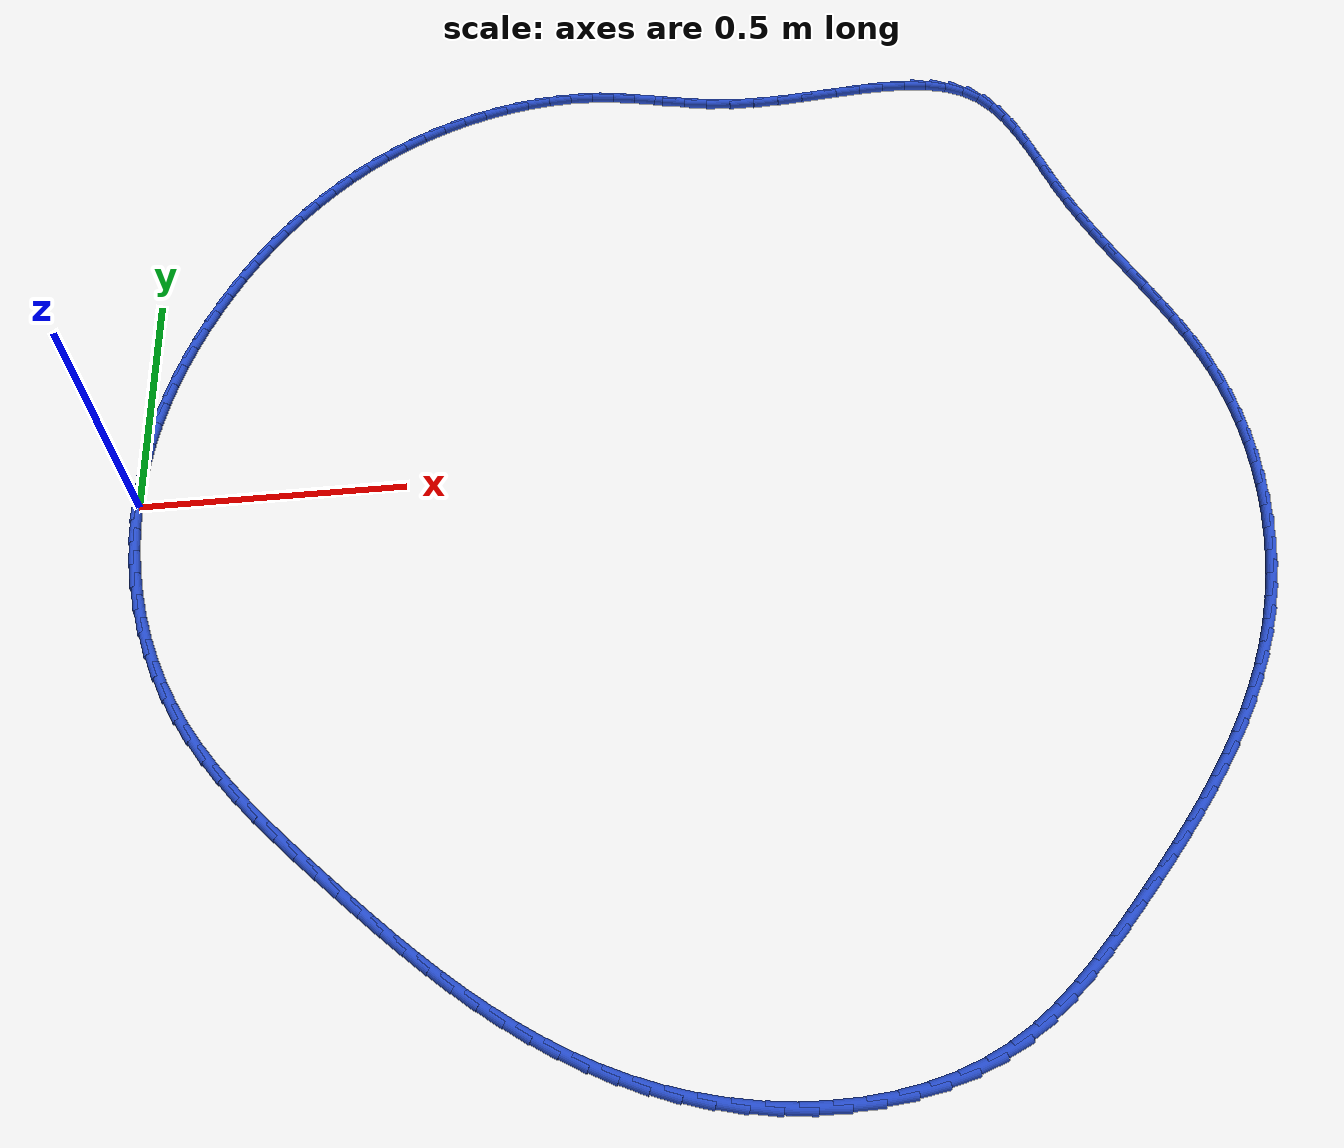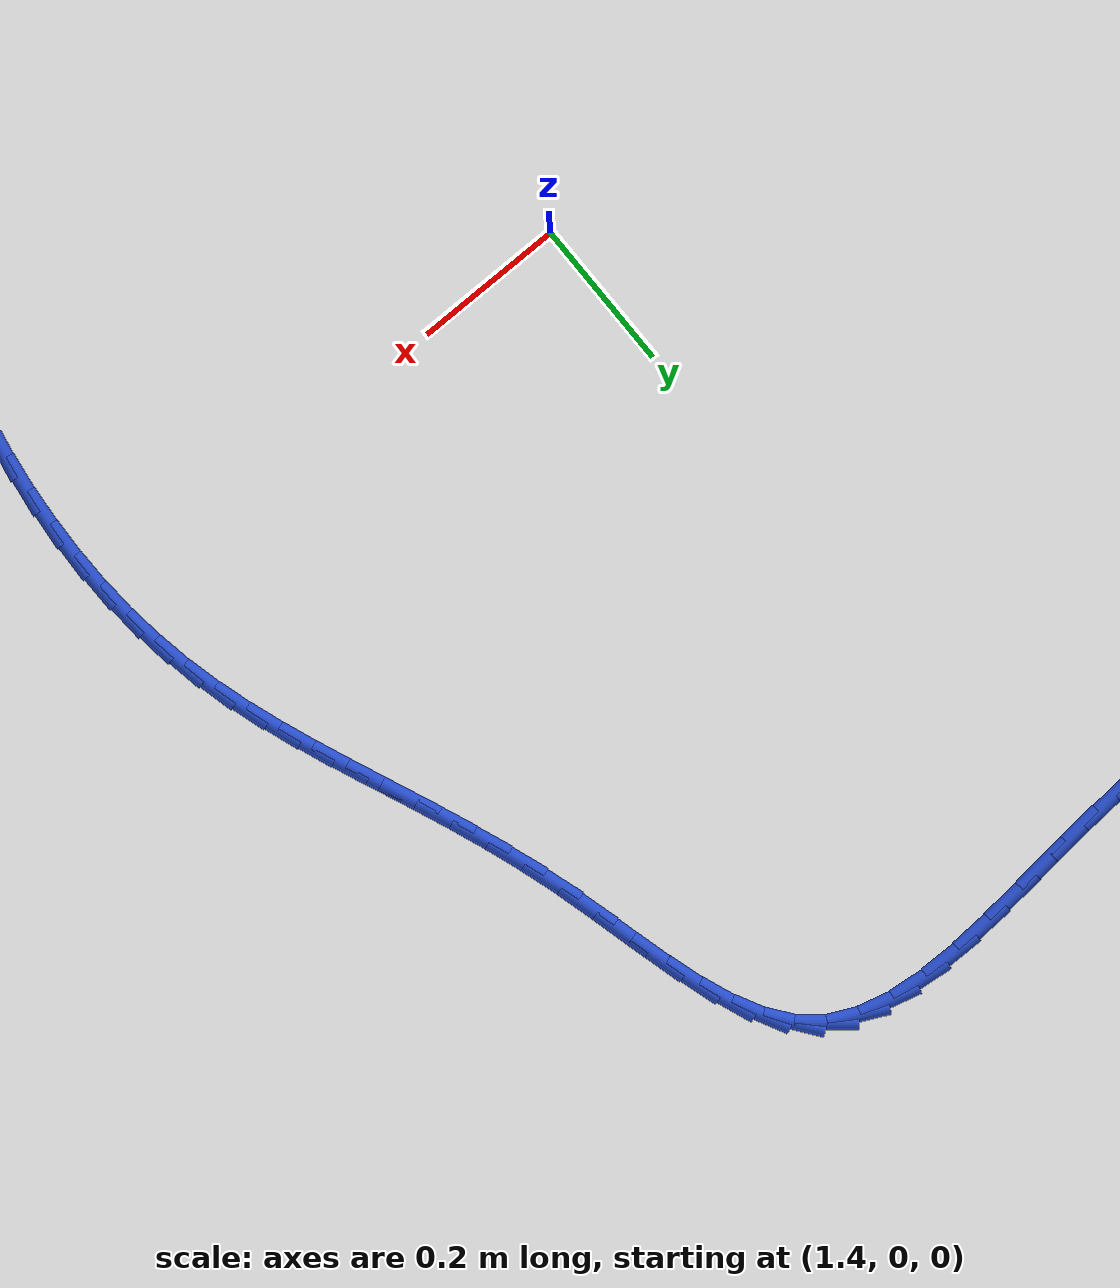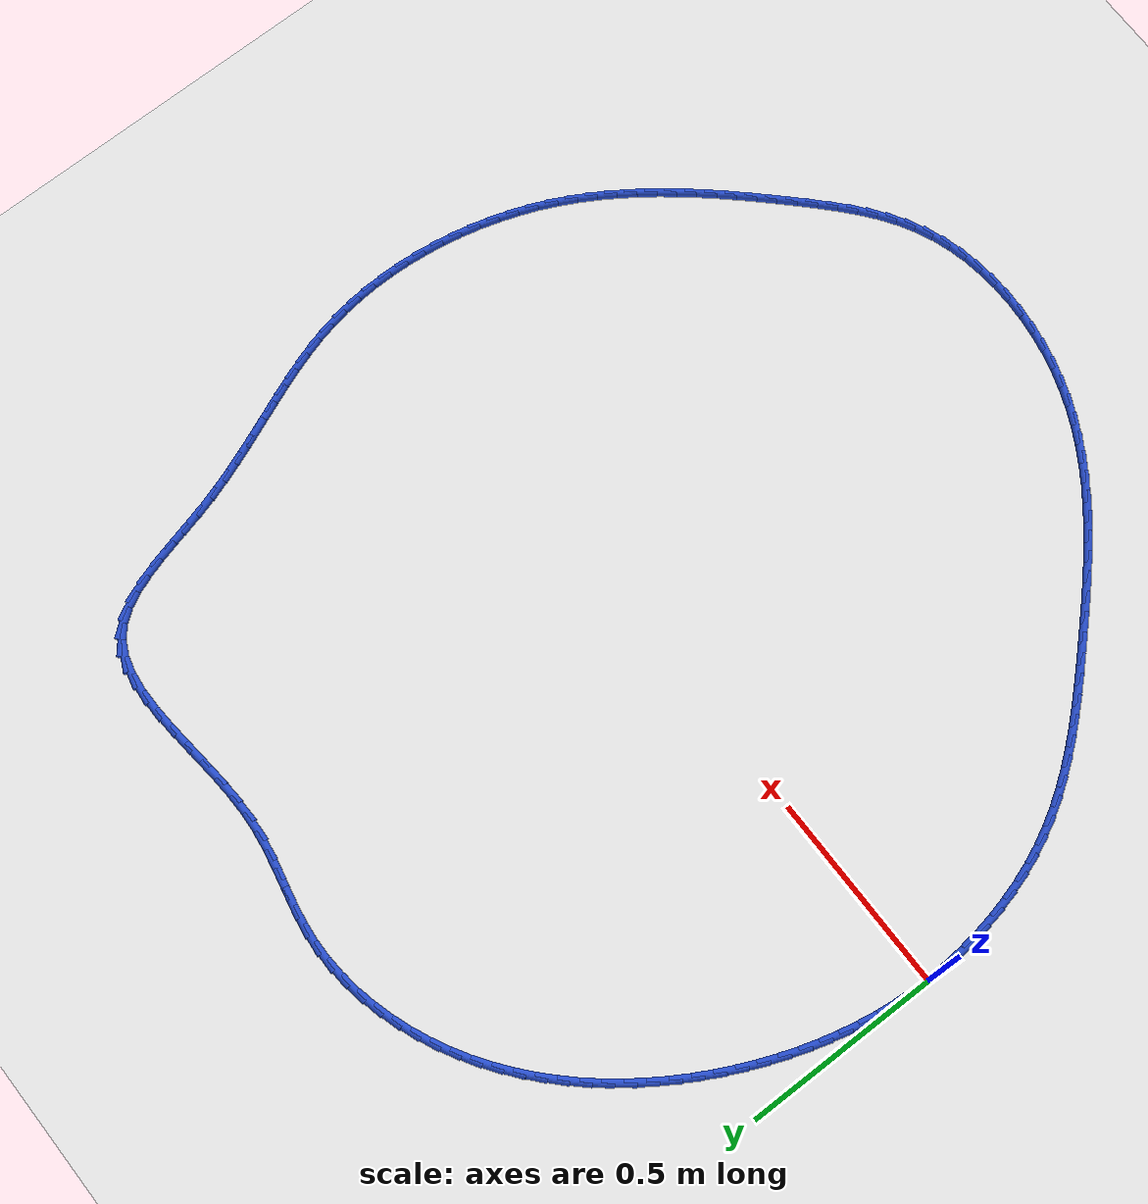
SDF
<sdf version="1.6">
 <world name="default">
  <light name="sun" type="directional">
   <pose>0 0 10 0 -0 0</pose>
   <diffuse>0.8 0.8 0.8 1</diffuse>
   <specular>0.2 0.2 0.2 1</specular>
   <attenuation>
    <range>1000</range>
    <constant>0.9</constant>
    <linear>0.01</linear>
    <quadratic>0.001</quadratic>
   </attenuation>
   <direction>-0.5 0.1 -0.9</direction>
  </light>
  <model name="ground_plane">
   <static>1</static>
   <link name="link">
    <collision name="collision">
     <geometry><plane><normal>0 0 1</normal><size>100 100</size></plane></geometry>
     <surface><friction><ode><mu>100</mu><mu2>50</mu2></ode></friction></surface>
    </collision>
    <visual name="visual">
     <cast_shadows>0</cast_shadows>
     <geometry><plane><normal>0 0 1</normal><size>100 100</size></plane></geometry>
     <material>
      <script><uri>file://media/materials/scripts/gazebo.material</uri><name>Gazebo/WhiteGlow</name></script>
     </material>
    </visual>
   </link>
  </model>
  <gravity>0 0 -9.8</gravity>
  <magnetic_field>6e-06 2.3e-05 -4.2e-05</magnetic_field>
  <atmosphere type="adiabatic"/>
  <physics name="default_physics" default="0" type="ode">
   <max_step_size>0.001</max_step_size>
   <real_time_factor>1</real_time_factor>
   <real_time_update_rate>1000</real_time_update_rate>
  </physics>
  <scene><ambient>0.4 0.4 0.4 1</ambient><background>0.7 0.7 0.7 1</background><shadows>1</shadows></scene>
  <spherical_coordinates>
   <surface_model>EARTH_WGS84</surface_model>
   <latitude_deg>0</latitude_deg>
   <longitude_deg>0</longitude_deg>
   <elevation>0</elevation>
   <heading_deg>0</heading_deg>
  </spherical_coordinates>
  <model name="line">
   <link name="link_0">
    <pose>-1.5612511283791264e-17 2.7755575615628914e-17 0.01 0 1.57 1.5340336237660577</pose>
    <collision name="collision">
     <geometry><cylinder><radius>0.01</radius><length>0.08</length></cylinder></geometry>
    </collision>
    <visual name="visual">
     <material>
      <script><name>Gazebo/Blue</name><uri>file://media/materials/scripts/gazebo.material</uri></script>
     </material>
     <geometry><cylinder><radius>0.01</radius><length>0.08</length></cylinder></geometry>
    </visual>
   </link>
   <link name="link_1">
    <pose>0.001806210534411196 0.04910946738691039 0.01 0 1.57 1.4845924661843406</pose>
    <collision name="collision">
     <geometry><cylinder><radius>0.01</radius><length>0.08</length></cylinder></geometry>
    </collision>
    <visual name="visual">
     <material>
      <script><name>Gazebo/Blue</name><uri>file://media/materials/scripts/gazebo.material</uri></script>
     </material>
     <geometry><cylinder><radius>0.01</radius><length>0.08</length></cylinder></geometry>
    </visual>
   </link>
   <link name="link_2">
    <pose>0.006025018215612498 0.0979280740659101 0.01 0 1.57 1.4364262405469406</pose>
    <collision name="collision">
     <geometry><cylinder><radius>0.01</radius><length>0.08</length></cylinder></geometry>
    </collision>
    <visual name="visual">
     <material>
      <script><name>Gazebo/Blue</name><uri>file://media/materials/scripts/gazebo.material</uri></script>
     </material>
     <geometry><cylinder><radius>0.01</radius><length>0.08</length></cylinder></geometry>
    </visual>
   </link>
   <link name="link_3">
    <pose>0.01258066853368429 0.14642211123359594 0.01 0 1.57 1.389640378000195</pose>
    <collision name="collision">
     <geometry><cylinder><radius>0.01</radius><length>0.08</length></cylinder></geometry>
    </collision>
    <visual name="visual">
     <material>
      <script><name>Gazebo/Blue</name><uri>file://media/materials/scripts/gazebo.material</uri></script>
     </material>
     <geometry><cylinder><radius>0.01</radius><length>0.08</length></cylinder></geometry>
    </visual>
   </link>
   <link name="link_4">
    <pose>0.021397406978706967 0.19455787008656475 0.01 0 1.57 1.3443101391814638</pose>
    <collision name="collision">
     <geometry><cylinder><radius>0.01</radius><length>0.08</length></cylinder></geometry>
    </collision>
    <visual name="visual">
     <material>
      <script><name>Gazebo/Blue</name><uri>file://media/materials/scripts/gazebo.material</uri></script>
     </material>
     <geometry><cylinder><radius>0.01</radius><length>0.08</length></cylinder></geometry>
    </visual>
   </link>
   <link name="link_5">
    <pose>0.03239947904076093 0.24230164182141323 0.01 0 1.57 1.3004824954389544</pose>
    <collision name="collision">
     <geometry><cylinder><radius>0.01</radius><length>0.08</length></cylinder></geometry>
    </collision>
    <visual name="visual">
     <material>
      <script><name>Gazebo/Blue</name><uri>file://media/materials/scripts/gazebo.material</uri></script>
     </material>
     <geometry><cylinder><radius>0.01</radius><length>0.08</length></cylinder></geometry>
    </visual>
   </link>
   <link name="link_6">
    <pose>0.04551113020992659 0.2896197176347382 0.01 0 1.57 1.2581787716653268</pose>
    <collision name="collision">
     <geometry><cylinder><radius>0.01</radius><length>0.08</length></cylinder></geometry>
    </collision>
    <visual name="visual">
     <material>
      <script><name>Gazebo/Blue</name><uri>file://media/materials/scripts/gazebo.material</uri></script>
     </material>
     <geometry><cylinder><radius>0.01</radius><length>0.08</length></cylinder></geometry>
    </visual>
   </link>
   <link name="link_7">
    <pose>0.06065660597628432 0.3364783887231364 0.01 0 1.57 1.2173977443518147</pose>
    <collision name="collision">
     <geometry><cylinder><radius>0.01</radius><length>0.08</length></cylinder></geometry>
    </collision>
    <visual name="visual">
     <material>
      <script><name>Gazebo/Blue</name><uri>file://media/materials/scripts/gazebo.material</uri></script>
     </material>
     <geometry><cylinder><radius>0.01</radius><length>0.08</length></cylinder></geometry>
    </visual>
   </link>
   <link name="link_8">
    <pose>0.07776015182991455 0.38284394628320484 0.01 0 1.57 1.178118927013361</pose>
    <collision name="collision">
     <geometry><cylinder><radius>0.01</radius><length>0.08</length></cylinder></geometry>
    </collision>
    <visual name="visual">
     <material>
      <script><name>Gazebo/Blue</name><uri>file://media/materials/scripts/gazebo.material</uri></script>
     </material>
     <geometry><cylinder><radius>0.01</radius><length>0.08</length></cylinder></geometry>
    </visual>
   </link>
   <link name="link_9">
    <pose>0.09674601326089766 0.4286826815115401 0.01 0 1.57 1.1400669123256677</pose>
    <collision name="collision">
     <geometry><cylinder><radius>0.01</radius><length>0.08</length></cylinder></geometry>
    </collision>
    <visual name="visual">
     <material>
      <script><name>Gazebo/Blue</name><uri>file://media/materials/scripts/gazebo.material</uri></script>
     </material>
     <geometry><cylinder><radius>0.01</radius><length>0.08</length></cylinder></geometry>
    </visual>
   </link>
   <link name="link_10">
    <pose>0.1175456132553554 0.47394799593618836 0.01 0 1.57 1.1017952948312875</pose>
    <collision name="collision">
     <geometry><cylinder><radius>0.01</radius><length>0.08</length></cylinder></geometry>
    </collision>
    <visual name="visual">
     <material>
      <script><name>Gazebo/Blue</name><uri>file://media/materials/scripts/gazebo.material</uri></script>
     </material>
     <geometry><cylinder><radius>0.01</radius><length>0.08</length></cylinder></geometry>
    </visual>
   </link>
   <link name="link_11">
    <pose>0.14013092364548493 0.5185204716530416 0.01 0 1.57 1.0626469959545786</pose>
    <collision name="collision">
     <geometry><cylinder><radius>0.01</radius><length>0.08</length></cylinder></geometry>
    </collision>
    <visual name="visual">
     <material>
      <script><name>Gazebo/Blue</name><uri>file://media/materials/scripts/gazebo.material</uri></script>
     </material>
     <geometry><cylinder><radius>0.01</radius><length>0.08</length></cylinder></geometry>
    </visual>
   </link>
   <link name="link_12">
    <pose>0.16448814135845993 0.5622551446959256 0.01 0 1.57 1.0224310589619197</pose>
    <collision name="collision">
     <geometry><cylinder><radius>0.01</radius><length>0.08</length></cylinder></geometry>
    </collision>
    <visual name="visual">
     <material>
      <script><name>Gazebo/Blue</name><uri>file://media/materials/scripts/gazebo.material</uri></script>
     </material>
     <geometry><cylinder><radius>0.01</radius><length>0.08</length></cylinder></geometry>
    </visual>
   </link>
   <link name="link_13">
    <pose>0.19060347871479333 0.605007023454619 0.01 0 1.57 0.9809618449627048</pose>
    <collision name="collision">
     <geometry><cylinder><radius>0.01</radius><length>0.08</length></cylinder></geometry>
    </collision>
    <visual name="visual">
     <material>
      <script><name>Gazebo/Blue</name><uri>file://media/materials/scripts/gazebo.material</uri></script>
     </material>
     <geometry><cylinder><radius>0.01</radius><length>0.08</length></cylinder></geometry>
    </visual>
   </link>
   <link name="link_14">
    <pose>0.21846314803499808 0.646631116318901 0.01 0 1.57 0.9380595946571773</pose>
    <collision name="collision">
     <geometry><cylinder><radius>0.01</radius><length>0.08</length></cylinder></geometry>
    </collision>
    <visual name="visual">
     <material>
      <script><name>Gazebo/Blue</name><uri>file://media/materials/scripts/gazebo.material</uri></script>
     </material>
     <geometry><cylinder><radius>0.01</radius><length>0.08</length></cylinder></geometry>
    </visual>
   </link>
   <link name="link_15">
    <pose>0.2480533616395871 0.68698243167855 0.01 0 1.57 0.8935524918583924</pose>
    <collision name="collision">
     <geometry><cylinder><radius>0.01</radius><length>0.08</length></cylinder></geometry>
    </collision>
    <visual name="visual">
     <material>
      <script><name>Gazebo/Blue</name><uri>file://media/materials/scripts/gazebo.material</uri></script>
     </material>
     <geometry><cylinder><radius>0.01</radius><length>0.08</length></cylinder></geometry>
    </visual>
   </link>
   <link name="link_16">
    <pose>0.2793603318490733 0.7259159779233446 0.01 0 1.57 0.847279858856683</pose>
    <collision name="collision">
     <geometry><cylinder><radius>0.01</radius><length>0.08</length></cylinder></geometry>
    </collision>
    <visual name="visual">
     <material>
      <script><name>Gazebo/Blue</name><uri>file://media/materials/scripts/gazebo.material</uri></script>
     </material>
     <geometry><cylinder><radius>0.01</radius><length>0.08</length></cylinder></geometry>
    </visual>
   </link>
   <link name="link_17">
    <pose>0.3123702709839696 0.7632867634430639 0.01 0 1.57 0.7990966143693009</pose>
    <collision name="collision">
     <geometry><cylinder><radius>0.01</radius><length>0.08</length></cylinder></geometry>
    </collision>
    <visual name="visual">
     <material>
      <script><name>Gazebo/Blue</name><uri>file://media/materials/scripts/gazebo.material</uri></script>
     </material>
     <geometry><cylinder><radius>0.01</radius><length>0.08</length></cylinder></geometry>
    </visual>
   </link>
   <link name="link_18">
    <pose>0.34706939136478876 0.7989497966274863 0.01 0 1.57 0.7488790799188343</pose>
    <collision name="collision">
     <geometry><cylinder><radius>0.01</radius><length>0.08</length></cylinder></geometry>
    </collision>
    <visual name="visual">
     <material>
      <script><name>Gazebo/Blue</name><uri>file://media/materials/scripts/gazebo.material</uri></script>
     </material>
     <geometry><cylinder><radius>0.01</radius><length>0.08</length></cylinder></geometry>
    </visual>
   </link>
   <link name="link_19">
    <pose>0.38344390531204403 0.8327600858663909 0.01 0 1.57 0.6965321284541816</pose>
    <collision name="collision">
     <geometry><cylinder><radius>0.01</radius><length>0.08</length></cylinder></geometry>
    </collision>
    <visual name="visual">
     <material>
      <script><name>Gazebo/Blue</name><uri>file://media/materials/scripts/gazebo.material</uri></script>
     </material>
     <geometry><cylinder><radius>0.01</radius><length>0.08</length></cylinder></geometry>
    </visual>
   </link>
   <link name="link_20">
    <pose>0.421480025146248 0.8645726395495559 0.01 0 1.57 0.6419975166842645</pose>
    <collision name="collision">
     <geometry><cylinder><radius>0.01</radius><length>0.08</length></cylinder></geometry>
    </collision>
    <visual name="visual">
     <material>
      <script><name>Gazebo/Blue</name><uri>file://media/materials/scripts/gazebo.material</uri></script>
     </material>
     <geometry><cylinder><radius>0.01</radius><length>0.08</length></cylinder></geometry>
    </visual>
   </link>
   <link name="link_21">
    <pose>0.46116396318791375 0.8942424660667603 0.01 0 1.57 0.5852630229832181</pose>
    <collision name="collision">
     <geometry><cylinder><radius>0.01</radius><length>0.08</length></cylinder></geometry>
    </collision>
    <visual name="visual">
     <material>
      <script><name>Gazebo/Blue</name><uri>file://media/materials/scripts/gazebo.material</uri></script>
     </material>
     <geometry><cylinder><radius>0.01</radius><length>0.08</length></cylinder></geometry>
    </visual>
   </link>
   <link name="link_22">
    <pose>0.5024819317575542 0.9216245738077831 0.01 0 1.57 0.5263717332748417</pose>
    <collision name="collision">
     <geometry><cylinder><radius>0.01</radius><length>0.08</length></cylinder></geometry>
    </collision>
    <visual name="visual">
     <material>
      <script><name>Gazebo/Blue</name><uri>file://media/materials/scripts/gazebo.material</uri></script>
     </material>
     <geometry><cylinder><radius>0.01</radius><length>0.08</length></cylinder></geometry>
    </visual>
   </link>
   <link name="link_23">
    <pose>0.545420143175682 0.9465739711624023 0.01 0 1.57 0.4654362565554381</pose>
    <collision name="collision">
     <geometry><cylinder><radius>0.01</radius><length>0.08</length></cylinder></geometry>
    </collision>
    <visual name="visual">
     <material>
      <script><name>Gazebo/Blue</name><uri>file://media/materials/scripts/gazebo.material</uri></script>
     </material>
     <geometry><cylinder><radius>0.01</radius><length>0.08</length></cylinder></geometry>
    </visual>
   </link>
   <link name="link_24">
    <pose>0.5899637902003093 0.9689454750341889 0.01 0 1.57 0.4030818393115089</pose>
    <collision name="collision">
     <geometry><cylinder><radius>0.01</radius><length>0.08</length></cylinder></geometry>
    </collision>
    <visual name="visual">
     <material>
      <script><name>Gazebo/Blue</name><uri>file://media/materials/scripts/gazebo.material</uri></script>
     </material>
     <geometry><cylinder><radius>0.01</radius><length>0.08</length></cylinder></geometry>
    </visual>
   </link>
   <link name="link_25">
    <pose>0.6359947874496205 0.9885745054389112 0.01 0 1.57 0.3397435695490179</pose>
    <collision name="collision">
     <geometry><cylinder><radius>0.01</radius><length>0.08</length></cylinder></geometry>
    </collision>
    <visual name="visual">
     <material>
      <script><name>Gazebo/Blue</name><uri>file://media/materials/scripts/gazebo.material</uri></script>
     </material>
     <geometry><cylinder><radius>0.01</radius><length>0.08</length></cylinder></geometry>
    </visual>
   </link>
   <link name="link_26">
    <pose>0.6832044559369886 1.0052606866007574 0.01 0 1.57 0.27460073581641886</pose>
    <collision name="collision">
     <geometry><cylinder><radius>0.01</radius><length>0.08</length></cylinder></geometry>
    </collision>
    <visual name="visual">
     <material>
      <script><name>Gazebo/Blue</name><uri>file://media/materials/scripts/gazebo.material</uri></script>
     </material>
     <geometry><cylinder><radius>0.01</radius><length>0.08</length></cylinder></geometry>
    </visual>
   </link>
   <link name="link_27">
    <pose>0.7312635511018416 1.018799780279594 0.01 0 1.57 0.20671852256041323</pose>
    <collision name="collision">
     <geometry><cylinder><radius>0.01</radius><length>0.08</length></cylinder></geometry>
    </collision>
    <visual name="visual">
     <material>
      <script><name>Gazebo/Blue</name><uri>file://media/materials/scripts/gazebo.material</uri></script>
     </material>
     <geometry><cylinder><radius>0.01</radius><length>0.08</length></cylinder></geometry>
    </visual>
   </link>
   <link name="link_28">
    <pose>0.7798428283836071 1.0289875482352857 0.01 0 1.57 0.13515972217466835</pose>
    <collision name="collision">
     <geometry><cylinder><radius>0.01</radius><length>0.08</length></cylinder></geometry>
    </collision>
    <visual name="visual">
     <material>
      <script><name>Gazebo/Blue</name><uri>file://media/materials/scripts/gazebo.material</uri></script>
     </material>
     <geometry><cylinder><radius>0.01</radius><length>0.08</length></cylinder></geometry>
    </visual>
   </link>
   <link name="link_29">
    <pose>0.8286130432217133 1.0356197522276989 0.01 0 1.57 0.05899559973866759</pose>
    <collision name="collision">
     <geometry><cylinder><radius>0.01</radius><length>0.08</length></cylinder></geometry>
    </collision>
    <visual name="visual">
     <material>
      <script><name>Gazebo/Blue</name><uri>file://media/materials/scripts/gazebo.material</uri></script>
     </material>
     <geometry><cylinder><radius>0.01</radius><length>0.08</length></cylinder></geometry>
    </visual>
   </link>
   <link name="link_30">
    <pose>0.877244951055587 1.0384921540166991 0.01 0 1.57 -0.022660985699172367</pose>
    <collision name="collision">
     <geometry><cylinder><radius>0.01</radius><length>0.08</length></cylinder></geometry>
    </collision>
    <visual name="visual">
     <material>
      <script><name>Gazebo/Blue</name><uri>file://media/materials/scripts/gazebo.material</uri></script>
     </material>
     <geometry><cylinder><radius>0.01</radius><length>0.08</length></cylinder></geometry>
    </visual>
   </link>
   <link name="link_31">
    <pose>0.9254093073246565 1.037400515362152 0.01 0 1.57 -0.10724344335077675</pose>
    <collision name="collision">
     <geometry><cylinder><radius>0.01</radius><length>0.08</length></cylinder></geometry>
    </collision>
    <visual name="visual">
     <material>
      <script><name>Gazebo/Blue</name><uri>file://media/materials/scripts/gazebo.material</uri></script>
     </material>
     <geometry><cylinder><radius>0.01</radius><length>0.08</length></cylinder></geometry>
    </visual>
   </link>
   <link name="link_32">
    <pose>0.9728544262518912 1.0322927406359885 0.01 0 1.57 -0.1718294851512073</pose>
    <collision name="collision">
     <geometry><cylinder><radius>0.01</radius><length>0.08</length></cylinder></geometry>
    </collision>
    <visual name="visual">
     <material>
      <script><name>Gazebo/Blue</name><uri>file://media/materials/scripts/gazebo.material</uri></script>
     </material>
     <geometry><cylinder><radius>0.01</radius><length>0.08</length></cylinder></geometry>
    </visual>
   </link>
   <link name="link_33">
    <pose>1.0198488756852047 1.024137285871992 0.01 0 1.57 -0.2057585692204956</pose>
    <collision name="collision">
     <geometry><cylinder><radius>0.01</radius><length>0.08</length></cylinder></geometry>
    </collision>
    <visual name="visual">
     <material>
      <script><name>Gazebo/Blue</name><uri>file://media/materials/scripts/gazebo.material</uri></script>
     </material>
     <geometry><cylinder><radius>0.01</radius><length>0.08</length></cylinder></geometry>
    </visual>
   </link>
   <link name="link_34">
    <pose>1.0668751819172775 1.0143223170990465 0.01 0 1.57 -0.2090328938851627</pose>
    <collision name="collision">
     <geometry><cylinder><radius>0.01</radius><length>0.08</length></cylinder></geometry>
    </collision>
    <visual name="visual">
     <material>
      <script><name>Gazebo/Blue</name><uri>file://media/materials/scripts/gazebo.material</uri></script>
     </material>
     <geometry><cylinder><radius>0.01</radius><length>0.08</length></cylinder></geometry>
    </visual>
   </link>
   <link name="link_35">
    <pose>1.114416530803299 1.004237294171934 0.01 0 1.57 -0.1826487961973674</pose>
    <collision name="collision">
     <geometry><cylinder><radius>0.01</radius><length>0.08</length></cylinder></geometry>
    </collision>
    <visual name="visual">
     <material>
      <script><name>Gazebo/Blue</name><uri>file://media/materials/scripts/gazebo.material</uri></script>
     </material>
     <geometry><cylinder><radius>0.01</radius><length>0.08</length></cylinder></geometry>
    </visual>
   </link>
   <link name="link_36">
    <pose>1.1629561081984583 0.9952716769454366 0.01 0 1.57 -0.12837101444714635</pose>
    <collision name="collision">
     <geometry><cylinder><radius>0.01</radius><length>0.08</length></cylinder></geometry>
    </collision>
    <visual name="visual">
     <material>
      <script><name>Gazebo/Blue</name><uri>file://media/materials/scripts/gazebo.material</uri></script>
     </material>
     <geometry><cylinder><radius>0.01</radius><length>0.08</length></cylinder></geometry>
    </visual>
   </link>
   <link name="link_37">
    <pose>1.2129770999579457 0.9888149252743372 0.01 0 1.57 -0.0505261361255027</pose>
    <collision name="collision">
     <geometry><cylinder><radius>0.01</radius><length>0.08</length></cylinder></geometry>
    </collision>
    <visual name="visual">
     <material>
      <script><name>Gazebo/Blue</name><uri>file://media/materials/scripts/gazebo.material</uri></script>
     </material>
     <geometry><cylinder><radius>0.01</radius><length>0.08</length></cylinder></geometry>
    </visual>
   </link>
   <link name="link_38">
    <pose>1.2649301799941752 0.9861877008276493 0.01 0 1.57 0.022632750712963754</pose>
    <collision name="collision">
     <geometry><cylinder><radius>0.01</radius><length>0.08</length></cylinder></geometry>
    </collision>
    <visual name="visual">
     <material>
      <script><name>Gazebo/Blue</name><uri>file://media/materials/scripts/gazebo.material</uri></script>
     </material>
     <geometry><cylinder><radius>0.01</radius><length>0.08</length></cylinder></geometry>
    </visual>
   </link>
   <link name="link_39">
    <pose>1.3186483896153882 0.9874036993101006 0.01 0 1.57 0.07114611563243067</pose>
    <collision name="collision">
     <geometry><cylinder><radius>0.01</radius><length>0.08</length></cylinder></geometry>
    </collision>
    <visual name="visual">
     <material>
      <script><name>Gazebo/Blue</name><uri>file://media/materials/scripts/gazebo.material</uri></script>
     </material>
     <geometry><cylinder><radius>0.01</radius><length>0.08</length></cylinder></geometry>
    </visual>
   </link>
   <link name="link_40">
    <pose>1.373411804115698 0.9913064907643587 0.01 0 1.57 0.09759905182260828</pose>
    <collision name="collision">
     <geometry><cylinder><radius>0.01</radius><length>0.08</length></cylinder></geometry>
    </collision>
    <visual name="visual">
     <material>
      <script><name>Gazebo/Blue</name><uri>file://media/materials/scripts/gazebo.material</uri></script>
     </material>
     <geometry><cylinder><radius>0.01</radius><length>0.08</length></cylinder></geometry>
    </visual>
   </link>
   <link name="link_41">
    <pose>1.4284809697761993 0.9966983200906676 0.01 0 1.57 0.10364600065930506</pose>
    <collision name="collision">
     <geometry><cylinder><radius>0.01</radius><length>0.08</length></cylinder></geometry>
    </collision>
    <visual name="visual">
     <material>
      <script><name>Gazebo/Blue</name><uri>file://media/materials/scripts/gazebo.material</uri></script>
     </material>
     <geometry><cylinder><radius>0.01</radius><length>0.08</length></cylinder></geometry>
    </visual>
   </link>
   <link name="link_42">
    <pose>1.4831164328779862 1.0023814321892728 0.01 0 1.57 0.08910932639259764</pose>
    <collision name="collision">
     <geometry><cylinder><radius>0.01</radius><length>0.08</length></cylinder></geometry>
    </collision>
    <visual name="visual">
     <material>
      <script><name>Gazebo/Blue</name><uri>file://media/materials/scripts/gazebo.material</uri></script>
     </material>
     <geometry><cylinder><radius>0.01</radius><length>0.08</length></cylinder></geometry>
    </visual>
   </link>
   <link name="link_43">
    <pose>1.5365787397021542 1.007158071960419 0.01 0 1.57 0.051795108233766894</pose>
    <collision name="collision">
     <geometry><cylinder><radius>0.01</radius><length>0.08</length></cylinder></geometry>
    </collision>
    <visual name="visual">
     <material>
      <script><name>Gazebo/Blue</name><uri>file://media/materials/scripts/gazebo.material</uri></script>
     </material>
     <geometry><cylinder><radius>0.01</radius><length>0.08</length></cylinder></geometry>
    </visual>
   </link>
   <link name="link_44">
    <pose>1.588128436529798 1.009830484304351 0.01 0 1.57 -0.012874557681891226</pose>
    <collision name="collision">
     <geometry><cylinder><radius>0.01</radius><length>0.08</length></cylinder></geometry>
    </collision>
    <visual name="visual">
     <material>
      <script><name>Gazebo/Blue</name><uri>file://media/materials/scripts/gazebo.material</uri></script>
     </material>
     <geometry><cylinder><radius>0.01</radius><length>0.08</length></cylinder></geometry>
    </visual>
   </link>
   <link name="link_45">
    <pose>1.6370260696420118 1.009200914121314 0.01 0 1.57 -0.11224313600365854</pose>
    <collision name="collision">
     <geometry><cylinder><radius>0.01</radius><length>0.08</length></cylinder></geometry>
    </collision>
    <visual name="visual">
     <material>
      <script><name>Gazebo/Blue</name><uri>file://media/materials/scripts/gazebo.material</uri></script>
     </material>
     <geometry><cylinder><radius>0.01</radius><length>0.08</length></cylinder></geometry>
    </visual>
   </link>
   <link name="link_46">
    <pose>1.682532185319891 1.0040716063115531 0.01 0 1.57 -0.25593544317708505</pose>
    <collision name="collision">
     <geometry><cylinder><radius>0.01</radius><length>0.08</length></cylinder></geometry>
    </collision>
    <visual name="visual">
     <material>
      <script><name>Gazebo/Blue</name><uri>file://media/materials/scripts/gazebo.material</uri></script>
     </material>
     <geometry><cylinder><radius>0.01</radius><length>0.08</length></cylinder></geometry>
    </visual>
   </link>
   <link name="link_47">
    <pose>1.72390732984453 0.9932448057753132 0.01 0 1.57 -0.4519584518205847</pose>
    <collision name="collision">
     <geometry><cylinder><radius>0.01</radius><length>0.08</length></cylinder></geometry>
    </collision>
    <visual name="visual">
     <material>
      <script><name>Gazebo/Blue</name><uri>file://media/materials/scripts/gazebo.material</uri></script>
     </material>
     <geometry><cylinder><radius>0.01</radius><length>0.08</length></cylinder></geometry>
    </visual>
   </link>
   <link name="link_48">
    <pose>1.7604120494970235 0.9755227574128389 0.01 0 1.57 -0.6951003165758325</pose>
    <collision name="collision">
     <geometry><cylinder><radius>0.01</radius><length>0.08</length></cylinder></geometry>
    </collision>
    <visual name="visual">
     <material>
      <script><name>Gazebo/Blue</name><uri>file://media/materials/scripts/gazebo.material</uri></script>
     </material>
     <geometry><cylinder><radius>0.01</radius><length>0.08</length></cylinder></geometry>
    </visual>
   </link>
   <link name="link_49">
    <pose>1.7913287196056 0.9497398938738197 0.01 0 1.57 -0.9276363154186914</pose>
    <collision name="collision">
     <geometry><cylinder><radius>0.01</radius><length>0.08</length></cylinder></geometry>
    </collision>
    <visual name="visual">
     <material>
      <script><name>Gazebo/Blue</name><uri>file://media/materials/scripts/gazebo.material</uri></script>
     </material>
     <geometry><cylinder><radius>0.01</radius><length>0.08</length></cylinder></geometry>
    </visual>
   </link>
   <link name="link_50">
    <pose>1.8167127292382912 0.9158704855855974 0.01 0 1.57 -1.0956185462248145</pose>
    <collision name="collision">
     <geometry><cylinder><radius>0.01</radius><length>0.08</length></cylinder></geometry>
    </collision>
    <visual name="visual">
     <material>
      <script><name>Gazebo/Blue</name><uri>file://media/materials/scripts/gazebo.material</uri></script>
     </material>
     <geometry><cylinder><radius>0.01</radius><length>0.08</length></cylinder></geometry>
    </visual>
   </link>
   <link name="link_51">
    <pose>1.8375819747790825 0.8753080561446405 0.01 0 1.57 -1.2069062894530147</pose>
    <collision name="collision">
     <geometry><cylinder><radius>0.01</radius><length>0.08</length></cylinder></geometry>
    </collision>
    <visual name="visual">
     <material>
      <script><name>Gazebo/Blue</name><uri>file://media/materials/scripts/gazebo.material</uri></script>
     </material>
     <geometry><cylinder><radius>0.01</radius><length>0.08</length></cylinder></geometry>
    </visual>
   </link>
   <link name="link_52">
    <pose>1.8550146523595699 0.829535043388871 0.01 0 1.57 -1.2751939807241766</pose>
    <collision name="collision">
     <geometry><cylinder><radius>0.01</radius><length>0.08</length></cylinder></geometry>
    </collision>
    <visual name="visual">
     <material>
      <script><name>Gazebo/Blue</name><uri>file://media/materials/scripts/gazebo.material</uri></script>
     </material>
     <geometry><cylinder><radius>0.01</radius><length>0.08</length></cylinder></geometry>
    </visual>
   </link>
   <link name="link_53">
    <pose>1.8700889581113471 0.7800338851562114 0.01 0 1.57 -1.3102847632019683</pose>
    <collision name="collision">
     <geometry><cylinder><radius>0.01</radius><length>0.08</length></cylinder></geometry>
    </collision>
    <visual name="visual">
     <material>
      <script><name>Gazebo/Blue</name><uri>file://media/materials/scripts/gazebo.material</uri></script>
     </material>
     <geometry><cylinder><radius>0.01</radius><length>0.08</length></cylinder></geometry>
    </visual>
   </link>
   <link name="link_54">
    <pose>1.8838830881660105 0.7282870192845833 0.01 0 1.57 -1.3175075034846024</pose>
    <collision name="collision">
     <geometry><cylinder><radius>0.01</radius><length>0.08</length></cylinder></geometry>
    </collision>
    <visual name="visual">
     <material>
      <script><name>Gazebo/Blue</name><uri>file://media/materials/scripts/gazebo.material</uri></script>
     </material>
     <geometry><cylinder><radius>0.01</radius><length>0.08</length></cylinder></geometry>
    </visual>
   </link>
   <link name="link_55">
    <pose>1.8974752386551543 0.6757768836119082 0.01 0 1.57 -1.2983949188859885</pose>
    <collision name="collision">
     <geometry><cylinder><radius>0.01</radius><length>0.08</length></cylinder></geometry>
    </collision>
    <visual name="visual">
     <material>
      <script><name>Gazebo/Blue</name><uri>file://media/materials/scripts/gazebo.material</uri></script>
     </material>
     <geometry><cylinder><radius>0.01</radius><length>0.08</length></cylinder></geometry>
    </visual>
   </link>
   <link name="link_56">
    <pose>1.911942998328892 0.623985195552956 0.01 0 1.57 -1.2600994673681414</pose>
    <collision name="collision">
     <geometry><cylinder><radius>0.01</radius><length>0.08</length></cylinder></geometry>
    </collision>
    <visual name="visual">
     <material>
      <script><name>Gazebo/Blue</name><uri>file://media/materials/scripts/gazebo.material</uri></script>
     </material>
     <geometry><cylinder><radius>0.01</radius><length>0.08</length></cylinder></geometry>
    </visual>
   </link>
   <link name="link_57">
    <pose>1.9280038055478947 0.5739664934145499 0.01 0 1.57 -1.2252017930950996</pose>
    <collision name="collision">
     <geometry><cylinder><radius>0.01</radius><length>0.08</length></cylinder></geometry>
    </collision>
    <visual name="visual">
     <material>
      <script><name>Gazebo/Blue</name><uri>file://media/materials/scripts/gazebo.material</uri></script>
     </material>
     <geometry><cylinder><radius>0.01</radius><length>0.08</length></cylinder></geometry>
    </visual>
   </link>
   <link name="link_58">
    <pose>1.9454077956750537 0.5256279847111204 0.01 0 1.57 -1.1983984559771772</pose>
    <collision name="collision">
     <geometry><cylinder><radius>0.01</radius><length>0.08</length></cylinder></geometry>
    </collision>
    <visual name="visual">
     <material>
      <script><name>Gazebo/Blue</name><uri>file://media/materials/scripts/gazebo.material</uri></script>
     </material>
     <geometry><cylinder><radius>0.01</radius><length>0.08</length></cylinder></geometry>
    </visual>
   </link>
   <link name="link_59">
    <pose>1.9637443824174403 0.4786862428898467 0.01 0 1.57 -1.1804117195987573</pose>
    <collision name="collision">
     <geometry><cylinder><radius>0.01</radius><length>0.08</length></cylinder></geometry>
    </collision>
    <visual name="visual">
     <material>
      <script><name>Gazebo/Blue</name><uri>file://media/materials/scripts/gazebo.material</uri></script>
     </material>
     <geometry><cylinder><radius>0.01</radius><length>0.08</length></cylinder></geometry>
    </visual>
   </link>
   <link name="link_60">
    <pose>1.982602979482125 0.43285784139791 0.01 0 1.57 -1.1718343408304202</pose>
    <collision name="collision">
     <geometry><cylinder><radius>0.01</radius><length>0.08</length></cylinder></geometry>
    </collision>
    <visual name="visual">
     <material>
      <script><name>Gazebo/Blue</name><uri>file://media/materials/scripts/gazebo.material</uri></script>
     </material>
     <geometry><cylinder><radius>0.01</radius><length>0.08</length></cylinder></geometry>
    </visual>
   </link>
   <link name="link_61">
    <pose>2.0015730005761783 0.3878593536824897 0.01 0 1.57 -1.1731488563914427</pose>
    <collision name="collision">
     <geometry><cylinder><radius>0.01</radius><length>0.08</length></cylinder></geometry>
    </collision>
    <visual name="visual">
     <material>
      <script><name>Gazebo/Blue</name><uri>file://media/materials/scripts/gazebo.material</uri></script>
     </material>
     <geometry><cylinder><radius>0.01</radius><length>0.08</length></cylinder></geometry>
    </visual>
   </link>
   <link name="link_62">
    <pose>2.0202438594066705 0.34340735319076665 0.01 0 1.57 -1.1847319859341918</pose>
    <collision name="collision">
     <geometry><cylinder><radius>0.01</radius><length>0.08</length></cylinder></geometry>
    </collision>
    <visual name="visual">
     <material>
      <script><name>Gazebo/Blue</name><uri>file://media/materials/scripts/gazebo.material</uri></script>
     </material>
     <geometry><cylinder><radius>0.01</radius><length>0.08</length></cylinder></geometry>
    </visual>
   </link>
   <link name="link_63">
    <pose>2.0382049696806734 0.2992184133699205 0.01 0 1.57 -1.2068344536608886</pose>
    <collision name="collision">
     <geometry><cylinder><radius>0.01</radius><length>0.08</length></cylinder></geometry>
    </collision>
    <visual name="visual">
     <material>
      <script><name>Gazebo/Blue</name><uri>file://media/materials/scripts/gazebo.material</uri></script>
     </material>
     <geometry><cylinder><radius>0.01</radius><length>0.08</length></cylinder></geometry>
    </visual>
   </link>
   <link name="link_64">
    <pose>2.0550457451052577 0.25500910766713214 0.01 0 1.57 -1.2395299507272333</pose>
    <collision name="collision">
     <geometry><cylinder><radius>0.01</radius><length>0.08</length></cylinder></geometry>
    </collision>
    <visual name="visual">
     <material>
      <script><name>Gazebo/Blue</name><uri>file://media/materials/scripts/gazebo.material</uri></script>
     </material>
     <geometry><cylinder><radius>0.01</radius><length>0.08</length></cylinder></geometry>
    </visual>
   </link>
   <link name="link_65">
    <pose>2.070355599387493 0.21049600952958136 0.01 0 1.57 -1.2826330570810893</pose>
    <collision name="collision">
     <geometry><cylinder><radius>0.01</radius><length>0.08</length></cylinder></geometry>
    </collision>
    <visual name="visual">
     <material>
      <script><name>Gazebo/Blue</name><uri>file://media/materials/scripts/gazebo.material</uri></script>
     </material>
     <geometry><cylinder><radius>0.01</radius><length>0.08</length></cylinder></geometry>
    </visual>
   </link>
   <link name="link_66">
    <pose>2.0837239462344512 0.16539569240444818 0.01 0 1.57 -1.3355964652234475</pose>
    <collision name="collision">
     <geometry><cylinder><radius>0.01</radius><length>0.08</length></cylinder></geometry>
    </collision>
    <visual name="visual">
     <material>
      <script><name>Gazebo/Blue</name><uri>file://media/materials/scripts/gazebo.material</uri></script>
     </material>
     <geometry><cylinder><radius>0.01</radius><length>0.08</length></cylinder></geometry>
    </visual>
   </link>
   <link name="link_67">
    <pose>2.094740199353203 0.11942472973891344 0.01 0 1.57 -1.395858333342795</pose>
    <collision name="collision">
     <geometry><cylinder><radius>0.01</radius><length>0.08</length></cylinder></geometry>
    </collision>
    <visual name="visual">
     <material>
      <script><name>Gazebo/Blue</name><uri>file://media/materials/scripts/gazebo.material</uri></script>
     </material>
     <geometry><cylinder><radius>0.01</radius><length>0.08</length></cylinder></geometry>
    </visual>
   </link>
   <link name="link_68">
    <pose>2.10305732266308 0.07236745115457911 0.01 0 1.57 -1.4551276186068844</pose>
    <collision name="collision">
     <geometry><cylinder><radius>0.01</radius><length>0.08</length></cylinder></geometry>
    </collision>
    <visual name="visual">
     <material>
      <script><name>Gazebo/Blue</name><uri>file://media/materials/scripts/gazebo.material</uri></script>
     </material>
     <geometry><cylinder><radius>0.01</radius><length>0.08</length></cylinder></geometry>
    </visual>
   </link>
   <link name="link_69">
    <pose>2.1086377239169805 0.02433811011774764 0.01 0 1.57 -1.511421228773499</pose>
    <collision name="collision">
     <geometry><cylinder><radius>0.01</radius><length>0.08</length></cylinder></geometry>
    </collision>
    <visual name="visual">
     <material>
      <script><name>Gazebo/Blue</name><uri>file://media/materials/scripts/gazebo.material</uri></script>
     </material>
     <geometry><cylinder><radius>0.01</radius><length>0.08</length></cylinder></geometry>
    </visual>
   </link>
   <link name="link_70">
    <pose>2.1115378584333295 -0.02444876796239864 0.01 0 1.57 -1.5651944066962005</pose>
    <collision name="collision">
     <geometry><cylinder><radius>0.01</radius><length>0.08</length></cylinder></geometry>
    </collision>
    <visual name="visual">
     <material>
      <script><name>Gazebo/Blue</name><uri>file://media/materials/scripts/gazebo.material</uri></script>
     </material>
     <geometry><cylinder><radius>0.01</radius><length>0.08</length></cylinder></geometry>
    </visual>
   </link>
   <link name="link_71">
    <pose>2.1118142032947085 -0.0737786344720963 0.01 0 1.57 1.5246943836477027</pose>
    <collision name="collision">
     <geometry><cylinder><radius>0.01</radius><length>0.08</length></cylinder></geometry>
    </collision>
    <visual name="visual">
     <material>
      <script><name>Gazebo/Blue</name><uri>file://media/materials/scripts/gazebo.material</uri></script>
     </material>
     <geometry><cylinder><radius>0.01</radius><length>0.08</length></cylinder></geometry>
    </visual>
   </link>
   <link name="link_72">
    <pose>2.109523235583701 -0.12343694079758319 0.01 0 1.57 1.4746183715994559</pose>
    <collision name="collision">
     <geometry><cylinder><radius>0.01</radius><length>0.08</length></cylinder></geometry>
    </collision>
    <visual name="visual">
     <material>
      <script><name>Gazebo/Blue</name><uri>file://media/materials/scripts/gazebo.material</uri></script>
     </material>
     <geometry><cylinder><radius>0.01</radius><length>0.08</length></cylinder></geometry>
    </visual>
   </link>
   <link name="link_73">
    <pose>2.104721432382888 -0.17320913832509752 0.01 0 1.57 1.4257394877952736</pose>
    <collision name="collision">
     <geometry><cylinder><radius>0.01</radius><length>0.08</length></cylinder></geometry>
    </collision>
    <visual name="visual">
     <material>
      <script><name>Gazebo/Blue</name><uri>file://media/materials/scripts/gazebo.material</uri></script>
     </material>
     <geometry><cylinder><radius>0.01</radius><length>0.08</length></cylinder></geometry>
    </visual>
   </link>
   <link name="link_74">
    <pose>2.097465270774854 -0.22288067844087514 0.01 0 1.57 1.3776361868793363</pose>
    <collision name="collision">
     <geometry><cylinder><radius>0.01</radius><length>0.08</length></cylinder></geometry>
    </collision>
    <visual name="visual">
     <material>
      <script><name>Gazebo/Blue</name><uri>file://media/materials/scripts/gazebo.material</uri></script>
     </material>
     <geometry><cylinder><radius>0.01</radius><length>0.08</length></cylinder></geometry>
    </visual>
   </link>
   <link name="link_75">
    <pose>2.087811227842178 -0.27223701253115423 0.01 0 1.57 1.3298928150577152</pose>
    <collision name="collision">
     <geometry><cylinder><radius>0.01</radius><length>0.08</length></cylinder></geometry>
    </collision>
    <visual name="visual">
     <material>
      <script><name>Gazebo/Blue</name><uri>file://media/materials/scripts/gazebo.material</uri></script>
     </material>
     <geometry><cylinder><radius>0.01</radius><length>0.08</length></cylinder></geometry>
    </visual>
   </link>
   <link name="link_76">
    <pose>2.075815780667444 -0.32106359198217227 0.01 0 1.57 1.2820952724784065</pose>
    <collision name="collision">
     <geometry><cylinder><radius>0.01</radius><length>0.08</length></cylinder></geometry>
    </collision>
    <visual name="visual">
     <material>
      <script><name>Gazebo/Blue</name><uri>file://media/materials/scripts/gazebo.material</uri></script>
     </material>
     <geometry><cylinder><radius>0.01</radius><length>0.08</length></cylinder></geometry>
    </visual>
   </link>
   <link name="link_77">
    <pose>2.0615354063332347 -0.3691458681801667 0.01 0 1.57 1.2338261303220057</pose>
    <collision name="collision">
     <geometry><cylinder><radius>0.01</radius><length>0.08</length></cylinder></geometry>
    </collision>
    <visual name="visual">
     <material>
      <script><name>Gazebo/Blue</name><uri>file://media/materials/scripts/gazebo.material</uri></script>
     </material>
     <geometry><cylinder><radius>0.01</radius><length>0.08</length></cylinder></geometry>
    </visual>
   </link>
   <link name="link_78">
    <pose>2.0450265819221305 -0.41626929251137557 0.01 0 1.57 1.1846596669359886</pose>
    <collision name="collision">
     <geometry><cylinder><radius>0.01</radius><length>0.08</length></cylinder></geometry>
    </collision>
    <visual name="visual">
     <material>
      <script><name>Gazebo/Blue</name><uri>file://media/materials/scripts/gazebo.material</uri></script>
     </material>
     <geometry><cylinder><radius>0.01</radius><length>0.08</length></cylinder></geometry>
    </visual>
   </link>
   <link name="link_79">
    <pose>2.0263457852430027 -0.462219318992902 0.01 0 1.57 1.1349348594426238</pose>
    <collision name="collision">
     <geometry><cylinder><radius>0.01</radius><length>0.08</length></cylinder></geometry>
    </collision>
    <visual name="visual">
     <material>
      <script><name>Gazebo/Blue</name><uri>file://media/materials/scripts/gazebo.material</uri></script>
     </material>
     <geometry><cylinder><radius>0.01</radius><length>0.08</length></cylinder></geometry>
    </visual>
   </link>
   <link name="link_80">
    <pose>2.005565195083401 -0.5068382760343407 0.01 0 1.57 1.0873161670758835</pose>
    <collision name="collision">
     <geometry><cylinder><radius>0.01</radius><length>0.08</length></cylinder></geometry>
    </collision>
    <visual name="visual">
     <material>
      <script><name>Gazebo/Blue</name><uri>file://media/materials/scripts/gazebo.material</uri></script>
     </material>
     <geometry><cylinder><radius>0.01</radius><length>0.08</length></cylinder></geometry>
    </visual>
   </link>
   <link name="link_81">
    <pose>1.9828131665091597 -0.5501719820165304 0.01 0 1.57 1.042703758907442</pose>
    <collision name="collision">
     <geometry><cylinder><radius>0.01</radius><length>0.08</length></cylinder></geometry>
    </collision>
    <visual name="visual">
     <material>
      <script><name>Gazebo/Blue</name><uri>file://media/materials/scripts/gazebo.material</uri></script>
     </material>
     <geometry><cylinder><radius>0.01</radius><length>0.08</length></cylinder></geometry>
    </visual>
   </link>
   <link name="link_82">
    <pose>1.9582306133185536 -0.5923117474066567 0.01 0 1.57 1.001337980167166</pose>
    <collision name="collision">
     <geometry><cylinder><radius>0.01</radius><length>0.08</length></cylinder></geometry>
    </collision>
    <visual name="visual">
     <material>
      <script><name>Gazebo/Blue</name><uri>file://media/materials/scripts/gazebo.material</uri></script>
     </material>
     <geometry><cylinder><radius>0.01</radius><length>0.08</length></cylinder></geometry>
    </visual>
   </link>
   <link name="link_83">
    <pose>1.9319584493098567 -0.6333488826719039 0.01 0 1.57 0.9633847790127246</pose>
    <collision name="collision">
     <geometry><cylinder><radius>0.01</radius><length>0.08</length></cylinder></geometry>
    </collision>
    <visual name="visual">
     <material>
      <script><name>Gazebo/Blue</name><uri>file://media/materials/scripts/gazebo.material</uri></script>
     </material>
     <geometry><cylinder><radius>0.01</radius><length>0.08</length></cylinder></geometry>
    </visual>
   </link>
   <link name="link_84">
    <pose>1.904137588281341 -0.6733746982794568 0.01 0 1.57 0.9289454710597488</pose>
    <collision name="collision">
     <geometry><cylinder><radius>0.01</radius><length>0.08</length></cylinder></geometry>
    </collision>
    <visual name="visual">
     <material>
      <script><name>Gazebo/Blue</name><uri>file://media/materials/scripts/gazebo.material</uri></script>
     </material>
     <geometry><cylinder><radius>0.01</radius><length>0.08</length></cylinder></geometry>
    </visual>
   </link>
   <link name="link_85">
    <pose>1.8749089440312803 -0.7124805046965013 0.01 0 1.57 0.8980685523963648</pose>
    <collision name="collision">
     <geometry><cylinder><radius>0.01</radius><length>0.08</length></cylinder></geometry>
    </collision>
    <visual name="visual">
     <material>
      <script><name>Gazebo/Blue</name><uri>file://media/materials/scripts/gazebo.material</uri></script>
     </material>
     <geometry><cylinder><radius>0.01</radius><length>0.08</length></cylinder></geometry>
    </visual>
   </link>
   <link name="link_86">
    <pose>1.8444134303579478 -0.750757612390222 0.01 0 1.57 0.8707620480177009</pose>
    <collision name="collision">
     <geometry><cylinder><radius>0.01</radius><length>0.08</length></cylinder></geometry>
    </collision>
    <visual name="visual">
     <material>
      <script><name>Gazebo/Blue</name><uri>file://media/materials/scripts/gazebo.material</uri></script>
     </material>
     <geometry><cylinder><radius>0.01</radius><length>0.08</length></cylinder></geometry>
    </visual>
   </link>
   <link name="link_87">
    <pose>1.8127919610596166 -0.7882973318278047 0.01 0 1.57 0.8470052985216541</pose>
    <collision name="collision">
     <geometry><cylinder><radius>0.01</radius><length>0.08</length></cylinder></geometry>
    </collision>
    <visual name="visual">
     <material>
      <script><name>Gazebo/Blue</name><uri>file://media/materials/scripts/gazebo.material</uri></script>
     </material>
     <geometry><cylinder><radius>0.01</radius><length>0.08</length></cylinder></geometry>
    </visual>
   </link>
   <link name="link_88">
    <pose>1.7801854499345608 -0.825190973476433 0.01 0 1.57 0.8267595057420533</pose>
    <collision name="collision">
     <geometry><cylinder><radius>0.01</radius><length>0.08</length></cylinder></geometry>
    </collision>
    <visual name="visual">
     <material>
      <script><name>Gazebo/Blue</name><uri>file://media/materials/scripts/gazebo.material</uri></script>
     </material>
     <geometry><cylinder><radius>0.01</radius><length>0.08</length></cylinder></geometry>
    </visual>
   </link>
   <link name="link_89">
    <pose>1.7467348107810527 -0.8615298478032929 0.01 0 1.57 0.8099767058446594</pose>
    <collision name="collision">
     <geometry><cylinder><radius>0.01</radius><length>0.08</length></cylinder></geometry>
    </collision>
    <visual name="visual">
     <material>
      <script><name>Gazebo/Blue</name><uri>file://media/materials/scripts/gazebo.material</uri></script>
     </material>
     <geometry><cylinder><radius>0.01</radius><length>0.08</length></cylinder></geometry>
    </visual>
   </link>
   <link name="link_90">
    <pose>1.7125809573973665 -0.8974052652755692 0.01 0 1.57 0.7966070889284098</pose>
    <collision name="collision">
     <geometry><cylinder><radius>0.01</radius><length>0.08</length></cylinder></geometry>
    </collision>
    <visual name="visual">
     <material>
      <script><name>Gazebo/Blue</name><uri>file://media/materials/scripts/gazebo.material</uri></script>
     </material>
     <geometry><cylinder><radius>0.01</radius><length>0.08</length></cylinder></geometry>
    </visual>
   </link>
   <link name="link_91">
    <pose>1.6778648035817745 -0.9329085363604479 0.01 0 1.57 0.7865780863257071</pose>
    <collision name="collision">
     <geometry><cylinder><radius>0.01</radius><length>0.08</length></cylinder></geometry>
    </collision>
    <visual name="visual">
     <material>
      <script><name>Gazebo/Blue</name><uri>file://media/materials/scripts/gazebo.material</uri></script>
     </material>
     <geometry><cylinder><radius>0.01</radius><length>0.08</length></cylinder></geometry>
    </visual>
   </link>
   <link name="link_92">
    <pose>1.6427265403020028 -0.9681298185196316 0.01 0 1.57 0.7748879341417741</pose>
    <collision name="collision">
     <geometry><cylinder><radius>0.01</radius><length>0.08</length></cylinder></geometry>
    </collision>
    <visual name="visual">
     <material>
      <script><name>Gazebo/Blue</name><uri>file://media/materials/scripts/gazebo.material</uri></script>
     </material>
     <geometry><cylinder><radius>0.01</radius><length>0.08</length></cylinder></geometry>
    </visual>
   </link>
   <link name="link_93">
    <pose>1.607171915315021 -1.002944815413491 0.01 0 1.57 0.7506419862285526</pose>
    <collision name="collision">
     <geometry><cylinder><radius>0.01</radius><length>0.08</length></cylinder></geometry>
    </collision>
    <visual name="visual">
     <material>
      <script><name>Gazebo/Blue</name><uri>file://media/materials/scripts/gazebo.material</uri></script>
     </material>
     <geometry><cylinder><radius>0.01</radius><length>0.08</length></cylinder></geometry>
    </visual>
   </link>
   <link name="link_94">
    <pose>1.5709154598820536 -1.036764703827637 0.01 0 1.57 0.7120081084481795</pose>
    <collision name="collision">
     <geometry><cylinder><radius>0.01</radius><length>0.08</length></cylinder></geometry>
    </collision>
    <visual name="visual">
     <material>
      <script><name>Gazebo/Blue</name><uri>file://media/materials/scripts/gazebo.material</uri></script>
     </material>
     <geometry><cylinder><radius>0.01</radius><length>0.08</length></cylinder></geometry>
    </visual>
   </link>
   <link name="link_95">
    <pose>1.5336336222612401 -1.0689399133762032 0.01 0 1.57 0.6583732010709324</pose>
    <collision name="collision">
     <geometry><cylinder><radius>0.01</radius><length>0.08</length></cylinder></geometry>
    </collision>
    <visual name="visual">
     <material>
      <script><name>Gazebo/Blue</name><uri>file://media/materials/scripts/gazebo.material</uri></script>
     </material>
     <geometry><cylinder><radius>0.01</radius><length>0.08</length></cylinder></geometry>
    </visual>
   </link>
   <link name="link_96">
    <pose>1.4950028507107207 -1.0988208736733214 0.01 0 1.57 0.5891749498678595</pose>
    <collision name="collision">
     <geometry><cylinder><radius>0.01</radius><length>0.08</length></cylinder></geometry>
    </collision>
    <visual name="visual">
     <material>
      <script><name>Gazebo/Blue</name><uri>file://media/materials/scripts/gazebo.material</uri></script>
     </material>
     <geometry><cylinder><radius>0.01</radius><length>0.08</length></cylinder></geometry>
    </visual>
   </link>
   <link name="link_97">
    <pose>1.4546995934886349 -1.1257580143331247 0.01 0 1.57 0.5042784827849761</pose>
    <collision name="collision">
     <geometry><cylinder><radius>0.01</radius><length>0.08</length></cylinder></geometry>
    </collision>
    <visual name="visual">
     <material>
      <script><name>Gazebo/Blue</name><uri>file://media/materials/scripts/gazebo.material</uri></script>
     </material>
     <geometry><cylinder><radius>0.01</radius><length>0.08</length></cylinder></geometry>
    </visual>
   </link>
   <link name="link_98">
    <pose>1.4124002988531212 -1.149101764969746 0.01 0 1.57 0.40746307798080894</pose>
    <collision name="collision">
     <geometry><cylinder><radius>0.01</radius><length>0.08</length></cylinder></geometry>
    </collision>
    <visual name="visual">
     <material>
      <script><name>Gazebo/Blue</name><uri>file://media/materials/scripts/gazebo.material</uri></script>
     </material>
     <geometry><cylinder><radius>0.01</radius><length>0.08</length></cylinder></geometry>
    </visual>
   </link>
   <link name="link_99">
    <pose>1.3678827063409744 -1.1683163753618857 0.01 0 1.57 0.31351237624140865</pose>
    <collision name="collision">
     <geometry><cylinder><radius>0.01</radius><length>0.08</length></cylinder></geometry>
    </collision>
    <visual name="visual">
     <material>
      <script><name>Gazebo/Blue</name><uri>file://media/materials/scripts/gazebo.material</uri></script>
     </material>
     <geometry><cylinder><radius>0.01</radius><length>0.08</length></cylinder></geometry>
    </visual>
   </link>
   <link name="link_100">
    <pose>1.3213902874313008 -1.1833894343853788 0.01 0 1.57 0.22624048906095473</pose>
    <collision name="collision">
     <geometry><cylinder><radius>0.01</radius><length>0.08</length></cylinder></geometry>
    </collision>
    <visual name="visual">
     <material>
      <script><name>Gazebo/Blue</name><uri>file://media/materials/scripts/gazebo.material</uri></script>
     </material>
     <geometry><cylinder><radius>0.01</radius><length>0.08</length></cylinder></geometry>
    </visual>
   </link>
   <link name="link_101">
    <pose>1.2733002855395148 -1.194458849324585 0.01 0 1.57 0.14506272170341514</pose>
    <collision name="collision">
     <geometry><cylinder><radius>0.01</radius><length>0.08</length></cylinder></geometry>
    </collision>
    <visual name="visual">
     <material>
      <script><name>Gazebo/Blue</name><uri>file://media/materials/scripts/gazebo.material</uri></script>
     </material>
     <geometry><cylinder><radius>0.01</radius><length>0.08</length></cylinder></geometry>
    </visual>
   </link>
   <link name="link_102">
    <pose>1.223989955734656 -1.201662540558949 0.01 0 1.57 0.0691944829307622</pose>
    <collision name="collision">
     <geometry><cylinder><radius>0.01</radius><length>0.08</length></cylinder></geometry>
    </collision>
    <visual name="visual">
     <material>
      <script><name>Gazebo/Blue</name><uri>file://media/materials/scripts/gazebo.material</uri></script>
     </material>
     <geometry><cylinder><radius>0.01</radius><length>0.08</length></cylinder></geometry>
    </visual>
   </link>
   <link name="link_103">
    <pose>1.173836553085766 -1.205138428467916 0.01 0 1.57 -0.002252007109569772</pose>
    <collision name="collision">
     <geometry><cylinder><radius>0.01</radius><length>0.08</length></cylinder></geometry>
    </collision>
    <visual name="visual">
     <material>
      <script><name>Gazebo/Blue</name><uri>file://media/materials/scripts/gazebo.material</uri></script>
     </material>
     <geometry><cylinder><radius>0.01</radius><length>0.08</length></cylinder></geometry>
    </visual>
   </link>
   <link name="link_104">
    <pose>1.1232173326618848 -1.2050244334309306 0.01 0 1.57 -0.07020808996304896</pose>
    <collision name="collision">
     <geometry><cylinder><radius>0.01</radius><length>0.08</length></cylinder></geometry>
    </collision>
    <visual name="visual">
     <material>
      <script><name>Gazebo/Blue</name><uri>file://media/materials/scripts/gazebo.material</uri></script>
     </material>
     <geometry><cylinder><radius>0.01</radius><length>0.08</length></cylinder></geometry>
    </visual>
   </link>
   <link name="link_105">
    <pose>1.0725095495320538 -1.2014584758274367 0.01 0 1.57 -0.13561863064074142</pose>
    <collision name="collision">
     <geometry><cylinder><radius>0.01</radius><length>0.08</length></cylinder></geometry>
    </collision>
    <visual name="visual">
     <material>
      <script><name>Gazebo/Blue</name><uri>file://media/materials/scripts/gazebo.material</uri></script>
     </material>
     <geometry><cylinder><radius>0.01</radius><length>0.08</length></cylinder></geometry>
    </visual>
   </link>
   <link name="link_106">
    <pose>1.022090458765314 -1.1945784760368798 0.01 0 1.57 -0.1994335019708749</pose>
    <collision name="collision">
     <geometry><cylinder><radius>0.01</radius><length>0.08</length></cylinder></geometry>
    </collision>
    <visual name="visual">
     <material>
      <script><name>Gazebo/Blue</name><uri>file://media/materials/scripts/gazebo.material</uri></script>
     </material>
     <geometry><cylinder><radius>0.01</radius><length>0.08</length></cylinder></geometry>
    </visual>
   </link>
   <link name="link_107">
    <pose>0.9723373154307057 -1.1845223544387042 0.01 0 1.57 -0.26261392025755304</pose>
    <collision name="collision">
     <geometry><cylinder><radius>0.01</radius><length>0.08</length></cylinder></geometry>
    </collision>
    <visual name="visual">
     <material>
      <script><name>Gazebo/Blue</name><uri>file://media/materials/scripts/gazebo.material</uri></script>
     </material>
     <geometry><cylinder><radius>0.01</radius><length>0.08</length></cylinder></geometry>
    </visual>
   </link>
   <link name="link_108">
    <pose>0.9236273745972696 -1.1714280314123542 0.01 0 1.57 -0.3261212047789748</pose>
    <collision name="collision">
     <geometry><cylinder><radius>0.01</radius><length>0.08</length></cylinder></geometry>
    </collision>
    <visual name="visual">
     <material>
      <script><name>Gazebo/Blue</name><uri>file://media/materials/scripts/gazebo.material</uri></script>
     </material>
     <geometry><cylinder><radius>0.01</radius><length>0.08</length></cylinder></geometry>
    </visual>
   </link>
   <link name="link_109">
    <pose>0.8763348553531035 -1.1554338561496933 0.01 0 1.57 -0.3890983101071305</pose>
    <collision name="collision">
     <geometry><cylinder><radius>0.01</radius><length>0.08</length></cylinder></geometry>
    </collision>
    <visual name="visual">
     <material>
      <script><name>Gazebo/Blue</name><uri>file://media/materials/scripts/gazebo.material</uri></script>
     </material>
     <geometry><cylinder><radius>0.01</radius><length>0.08</length></cylinder></geometry>
    </visual>
   </link>
   <link name="link_110">
    <pose>0.8306520961407301 -1.1367038672921963 0.01 0 1.57 -0.4486972834981993</pose>
    <collision name="collision">
     <geometry><cylinder><radius>0.01</radius><length>0.08</length></cylinder></geometry>
    </collision>
    <visual name="visual">
     <material>
      <script><name>Gazebo/Blue</name><uri>file://media/materials/scripts/gazebo.material</uri></script>
     </material>
     <geometry><cylinder><radius>0.01</radius><length>0.08</length></cylinder></geometry>
    </visual>
   </link>
   <link name="link_111">
    <pose>0.7864896802570989 -1.115441899549755 0.01 0 1.57 -0.5041181809997564</pose>
    <collision name="collision">
     <geometry><cylinder><radius>0.01</radius><length>0.08</length></cylinder></geometry>
    </collision>
    <visual name="visual">
     <material>
      <script><name>Gazebo/Blue</name><uri>file://media/materials/scripts/gazebo.material</uri></script>
     </material>
     <geometry><cylinder><radius>0.01</radius><length>0.08</length></cylinder></geometry>
    </visual>
   </link>
   <link name="link_112">
    <pose>0.7437339726711542 -1.0918552083124287 0.01 0 1.57 -0.5549491424522279</pose>
    <collision name="collision">
     <geometry><cylinder><radius>0.01</radius><length>0.08</length></cylinder></geometry>
    </collision>
    <visual name="visual">
     <material>
      <script><name>Gazebo/Blue</name><uri>file://media/materials/scripts/gazebo.material</uri></script>
     </material>
     <geometry><cylinder><radius>0.01</radius><length>0.08</length></cylinder></geometry>
    </visual>
   </link>
   <link name="link_113">
    <pose>0.70227133835184 -1.0661510489702757 0.01 0 1.57 -0.6009320600229929</pose>
    <collision name="collision">
     <geometry><cylinder><radius>0.01</radius><length>0.08</length></cylinder></geometry>
    </collision>
    <visual name="visual">
     <material>
      <script><name>Gazebo/Blue</name><uri>file://media/materials/scripts/gazebo.material</uri></script>
     </material>
     <geometry><cylinder><radius>0.01</radius><length>0.08</length></cylinder></geometry>
    </visual>
   </link>
   <link name="link_114">
    <pose>0.6619881422681015 -1.038536676913355 0.01 0 1.57 -0.6419372726688846</pose>
    <collision name="collision">
     <geometry><cylinder><radius>0.01</radius><length>0.08</length></cylinder></geometry>
    </collision>
    <visual name="visual">
     <material>
      <script><name>Gazebo/Blue</name><uri>file://media/materials/scripts/gazebo.material</uri></script>
     </material>
     <geometry><cylinder><radius>0.01</radius><length>0.08</length></cylinder></geometry>
    </visual>
   </link>
   <link name="link_115">
    <pose>0.6227707493888833 -1.0092193475317257 0.01 0 1.57 -0.6779333255197937</pose>
    <collision name="collision">
     <geometry><cylinder><radius>0.01</radius><length>0.08</length></cylinder></geometry>
    </collision>
    <visual name="visual">
     <material>
      <script><name>Gazebo/Blue</name><uri>file://media/materials/scripts/gazebo.material</uri></script>
     </material>
     <geometry><cylinder><radius>0.01</radius><length>0.08</length></cylinder></geometry>
    </visual>
   </link>
   <link name="link_116">
    <pose>0.5845055246831296 -0.9784063162154466 0.01 0 1.57 -0.7089566660092739</pose>
    <collision name="collision">
     <geometry><cylinder><radius>0.01</radius><length>0.08</length></cylinder></geometry>
    </collision>
    <visual name="visual">
     <material>
      <script><name>Gazebo/Blue</name><uri>file://media/materials/scripts/gazebo.material</uri></script>
     </material>
     <geometry><cylinder><radius>0.01</radius><length>0.08</length></cylinder></geometry>
    </visual>
   </link>
   <link name="link_117">
    <pose>0.5470788331197843 -0.9463048383545754 0.01 0 1.57 -0.7350843414214909</pose>
    <collision name="collision">
     <geometry><cylinder><radius>0.01</radius><length>0.08</length></cylinder></geometry>
    </collision>
    <visual name="visual">
     <material>
      <script><name>Gazebo/Blue</name><uri>file://media/materials/scripts/gazebo.material</uri></script>
     </material>
     <geometry><cylinder><radius>0.01</radius><length>0.08</length></cylinder></geometry>
    </visual>
   </link>
   <link name="link_118">
    <pose>0.5103770396677928 -0.9131221693391716 0.01 0 1.57 -0.7564111507568014</pose>
    <collision name="collision">
     <geometry><cylinder><radius>0.01</radius><length>0.08</length></cylinder></geometry>
    </collision>
    <visual name="visual">
     <material>
      <script><name>Gazebo/Blue</name><uri>file://media/materials/scripts/gazebo.material</uri></script>
     </material>
     <geometry><cylinder><radius>0.01</radius><length>0.08</length></cylinder></geometry>
    </visual>
   </link>
   <link name="link_119">
    <pose>0.4742865092960994 -0.8790655645592942 0.01 0 1.57 -0.7730315538321838</pose>
    <collision name="collision">
     <geometry><cylinder><radius>0.01</radius><length>0.08</length></cylinder></geometry>
    </collision>
    <visual name="visual">
     <material>
      <script><name>Gazebo/Blue</name><uri>file://media/materials/scripts/gazebo.material</uri></script>
     </material>
     <geometry><cylinder><radius>0.01</radius><length>0.08</length></cylinder></geometry>
    </visual>
   </link>
   <link name="link_120">
    <pose>0.43869360697364845 -0.8443422794050015 0.01 0 1.57 -0.7850259718693596</pose>
    <collision name="collision">
     <geometry><cylinder><radius>0.01</radius><length>0.08</length></cylinder></geometry>
    </collision>
    <visual name="visual">
     <material>
      <script><name>Gazebo/Blue</name><uri>file://media/materials/scripts/gazebo.material</uri></script>
     </material>
     <geometry><cylinder><radius>0.01</radius><length>0.08</length></cylinder></geometry>
    </visual>
   </link>
   <link name="link_121">
    <pose>0.40348469766938433 -0.8091595692663522 0.01 0 1.57 -0.792471887474657</pose>
    <collision name="collision">
     <geometry><cylinder><radius>0.01</radius><length>0.08</length></cylinder></geometry>
    </collision>
    <visual name="visual">
     <material>
      <script><name>Gazebo/Blue</name><uri>file://media/materials/scripts/gazebo.material</uri></script>
     </material>
     <geometry><cylinder><radius>0.01</radius><length>0.08</length></cylinder></geometry>
    </visual>
   </link>
   <link name="link_122">
    <pose>0.36854688934298624 -0.7737239504307384 0.01 0 1.57 -0.7985898406414407</pose>
    <collision name="collision">
     <geometry><cylinder><radius>0.01</radius><length>0.08</length></cylinder></geometry>
    </collision>
    <visual name="visual">
     <material>
      <script><name>Gazebo/Blue</name><uri>file://media/materials/scripts/gazebo.material</uri></script>
     </material>
     <geometry><cylinder><radius>0.01</radius><length>0.08</length></cylinder></geometry>
    </visual>
   </link>
   <link name="link_123">
    <pose>0.3338798357462646 -0.7381299823452 0.01 0 1.57 -0.8100005408140426</pose>
    <collision name="collision">
     <geometry><cylinder><radius>0.01</radius><length>0.08</length></cylinder></geometry>
    </collision>
    <visual name="visual">
     <material>
      <script><name>Gazebo/Blue</name><uri>file://media/materials/scripts/gazebo.material</uri></script>
     </material>
     <geometry><cylinder><radius>0.01</radius><length>0.08</length></cylinder></geometry>
    </visual>
   </link>
   <link name="link_124">
    <pose>0.2997151525772188 -0.7022414763667242 0.01 0 1.57 -0.8276043705538363</pose>
    <collision name="collision">
     <geometry><cylinder><radius>0.01</radius><length>0.08</length></cylinder></geometry>
    </collision>
    <visual name="visual">
     <material>
      <script><name>Gazebo/Blue</name><uri>file://media/materials/scripts/gazebo.material</uri></script>
     </material>
     <geometry><cylinder><radius>0.01</radius><length>0.08</length></cylinder></geometry>
    </visual>
   </link>
   <link name="link_125">
    <pose>0.2663130741481002 -0.665893774999166 0.01 0 1.57 -0.8515202645048937</pose>
    <collision name="collision">
     <geometry><cylinder><radius>0.01</radius><length>0.08</length></cylinder></geometry>
    </collision>
    <visual name="visual">
     <material>
      <script><name>Gazebo/Blue</name><uri>file://media/materials/scripts/gazebo.material</uri></script>
     </material>
     <geometry><cylinder><radius>0.01</radius><length>0.08</length></cylinder></geometry>
    </visual>
   </link>
   <link name="link_126">
    <pose>0.2339338347711593 -0.6289222207463799 0.01 0 1.57 -0.8818775849640315</pose>
    <collision name="collision">
     <geometry><cylinder><radius>0.01</radius><length>0.08</length></cylinder></geometry>
    </collision>
    <visual name="visual">
     <material>
      <script><name>Gazebo/Blue</name><uri>file://media/materials/scripts/gazebo.material</uri></script>
     </material>
     <geometry><cylinder><radius>0.01</radius><length>0.08</length></cylinder></geometry>
    </visual>
   </link>
   <link name="link_127">
    <pose>0.2028376687586485 -0.5911621561122213 0.01 0 1.57 -0.9187876699716575</pose>
    <collision name="collision">
     <geometry><cylinder><radius>0.01</radius><length>0.08</length></cylinder></geometry>
    </collision>
    <visual name="visual">
     <material>
      <script><name>Gazebo/Blue</name><uri>file://media/materials/scripts/gazebo.material</uri></script>
     </material>
     <geometry><cylinder><radius>0.01</radius><length>0.08</length></cylinder></geometry>
    </visual>
   </link>
   <link name="link_128">
    <pose>0.17328481042281832 -0.5524489236005452 0.01 0 1.57 -0.9623051553802091</pose>
    <collision name="collision">
     <geometry><cylinder><radius>0.01</radius><length>0.08</length></cylinder></geometry>
    </collision>
    <visual name="visual">
     <material>
      <script><name>Gazebo/Blue</name><uri>file://media/materials/scripts/gazebo.material</uri></script>
     </material>
     <geometry><cylinder><radius>0.01</radius><length>0.08</length></cylinder></geometry>
    </visual>
   </link>
   <link name="link_129">
    <pose>0.14553549407592017 -0.5126178657152062 0.01 0 1.57 -1.0123793356162831</pose>
    <collision name="collision">
     <geometry><cylinder><radius>0.01</radius><length>0.08</length></cylinder></geometry>
    </collision>
    <visual name="visual">
     <material>
      <script><name>Gazebo/Blue</name><uri>file://media/materials/scripts/gazebo.material</uri></script>
     </material>
     <geometry><cylinder><radius>0.01</radius><length>0.08</length></cylinder></geometry>
    </visual>
   </link>
   <link name="link_130">
    <pose>0.11984995403020517 -0.47150432496005923 0.01 0 1.57 -1.068796446352719</pose>
    <collision name="collision">
     <geometry><cylinder><radius>0.01</radius><length>0.08</length></cylinder></geometry>
    </collision>
    <visual name="visual">
     <material>
      <script><name>Gazebo/Blue</name><uri>file://media/materials/scripts/gazebo.material</uri></script>
     </material>
     <geometry><cylinder><radius>0.01</radius><length>0.08</length></cylinder></geometry>
    </visual>
   </link>
   <link name="link_131">
    <pose>0.09648835814903743 -0.42894373516841194 0.01 0 1.57 -1.1292525179334914</pose>
    <collision name="collision">
     <geometry><cylinder><radius>0.01</radius><length>0.08</length></cylinder></geometry>
    </collision>
    <visual name="visual">
     <material>
      <script><name>Gazebo/Blue</name><uri>file://media/materials/scripts/gazebo.material</uri></script>
     </material>
     <geometry><cylinder><radius>0.01</radius><length>0.08</length></cylinder></geometry>
    </visual>
   </link>
   <link name="link_132">
    <pose>0.07564946840365175 -0.38485592837550253 0.01 0 1.57 -1.188193850124566</pose>
    <collision name="collision">
     <geometry><cylinder><radius>0.01</radius><length>0.08</length></cylinder></geometry>
    </collision>
    <visual name="visual">
     <material>
      <script><name>Gazebo/Blue</name><uri>file://media/materials/scripts/gazebo.material</uri></script>
     </material>
     <geometry><cylinder><radius>0.01</radius><length>0.08</length></cylinder></geometry>
    </visual>
   </link>
   <link name="link_133">
    <pose>0.05735700835097127 -0.3394013149539832 0.01 0 1.57 -1.2449236247940751</pose>
    <collision name="collision">
     <geometry><cylinder><radius>0.01</radius><length>0.08</length></cylinder></geometry>
    </collision>
    <visual name="visual">
     <material>
      <script><name>Gazebo/Blue</name><uri>file://media/materials/scripts/gazebo.material</uri></script>
     </material>
     <geometry><cylinder><radius>0.01</radius><length>0.08</length></cylinder></geometry>
    </visual>
   </link>
   <link name="link_134">
    <pose>0.04160371823649651 -0.29278288972049354 0.01 0 1.57 -1.2997534066307879</pose>
    <collision name="collision">
     <geometry><cylinder><radius>0.01</radius><length>0.08</length></cylinder></geometry>
    </collision>
    <visual name="visual">
     <material>
      <script><name>Gazebo/Blue</name><uri>file://media/materials/scripts/gazebo.material</uri></script>
     </material>
     <geometry><cylinder><radius>0.01</radius><length>0.08</length></cylinder></geometry>
    </visual>
   </link>
   <link name="link_135">
    <pose>0.028382338305727877 -0.2452036474916726 0.01 0 1.57 -1.3530115599060093</pose>
    <collision name="collision">
     <geometry><cylinder><radius>0.01</radius><length>0.08</length></cylinder></geometry>
    </collision>
    <visual name="visual">
     <material>
      <script><name>Gazebo/Blue</name><uri>file://media/materials/scripts/gazebo.material</uri></script>
     </material>
     <geometry><cylinder><radius>0.01</radius><length>0.08</length></cylinder></geometry>
    </visual>
   </link>
   <link name="link_136">
    <pose>0.01768560880416632 -0.19686658308416144 0.01 0 1.57 -1.4050369613968658</pose>
    <collision name="collision">
     <geometry><cylinder><radius>0.01</radius><length>0.08</length></cylinder></geometry>
    </collision>
    <visual name="visual">
     <material>
      <script><name>Gazebo/Blue</name><uri>file://media/materials/scripts/gazebo.material</uri></script>
     </material>
     <geometry><cylinder><radius>0.01</radius><length>0.08</length></cylinder></geometry>
    </visual>
   </link>
   <link name="link_137">
    <pose>0.009506269977312194 -0.14797469131459898 0.01 0 1.57 -1.4561754494256869</pose>
    <collision name="collision">
     <geometry><cylinder><radius>0.01</radius><length>0.08</length></cylinder></geometry>
    </collision>
    <visual name="visual">
     <material>
      <script><name>Gazebo/Blue</name><uri>file://media/materials/scripts/gazebo.material</uri></script>
     </material>
     <geometry><cylinder><radius>0.01</radius><length>0.08</length></cylinder></geometry>
    </visual>
   </link>
   <link name="link_138">
    <pose>0.0038370620706660585 -0.09873096699962494 0.01 0 1.57 -1.50677838767893</pose>
    <collision name="collision">
     <geometry><cylinder><radius>0.01</radius><length>0.08</length></cylinder></geometry>
    </collision>
    <visual name="visual">
     <material>
      <script><name>Gazebo/Blue</name><uri>file://media/materials/scripts/gazebo.material</uri></script>
     </material>
     <geometry><cylinder><radius>0.01</radius><length>0.08</length></cylinder></geometry>
    </visual>
   </link>
   <link name="link_139">
    <pose>0.0006707253297284603 -0.049338404955879045 0.01 0 1.57 -1.5572027779846156</pose>
    <collision name="collision">
     <geometry><cylinder><radius>0.01</radius><length>0.08</length></cylinder></geometry>
    </collision>
    <visual name="visual">
     <material>
      <script><name>Gazebo/Blue</name><uri>file://media/materials/scripts/gazebo.material</uri></script>
     </material>
     <geometry><cylinder><radius>0.01</radius><length>0.08</length></cylinder></geometry>
    </visual>
   </link>
   <link name="link_140">
    <pose>-1.5612511283791264e-17 -4.163336342344337e-17 0.01 0 1.57 1.533780236675863</pose>
    <collision name="collision">
     <geometry><cylinder><radius>0.01</radius><length>0.08</length></cylinder></geometry>
    </collision>
    <visual name="visual">
     <material>
      <script><name>Gazebo/Blue</name><uri>file://media/materials/scripts/gazebo.material</uri></script>
     </material>
     <geometry><cylinder><radius>0.01</radius><length>0.08</length></cylinder></geometry>
    </visual>
   </link>
   <link name="link_141">
    <pose>0.0018176263269812087 0.04908125305137068 0.01 0 1.57 1.533780236675863</pose>
    <collision name="collision">
     <geometry><cylinder><radius>0.01</radius><length>0.08</length></cylinder></geometry>
    </collision>
    <visual name="visual">
     <material>
      <script><name>Gazebo/Blue</name><uri>file://media/materials/scripts/gazebo.material</uri></script>
     </material>
     <geometry><cylinder><radius>0.01</radius><length>0.08</length></cylinder></geometry>
    </visual>
   </link>
  </model>
 </world>
</sdf>
